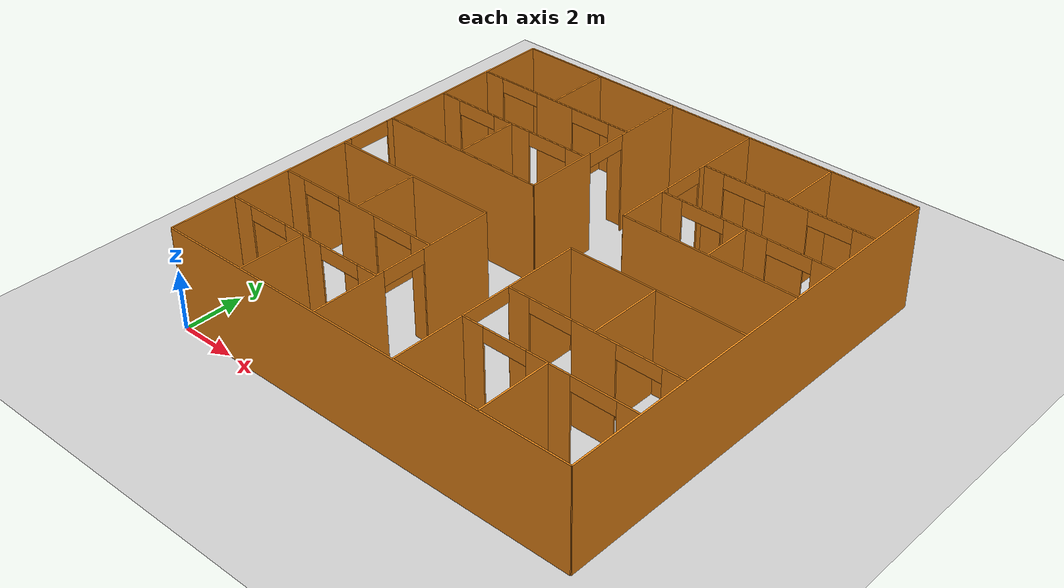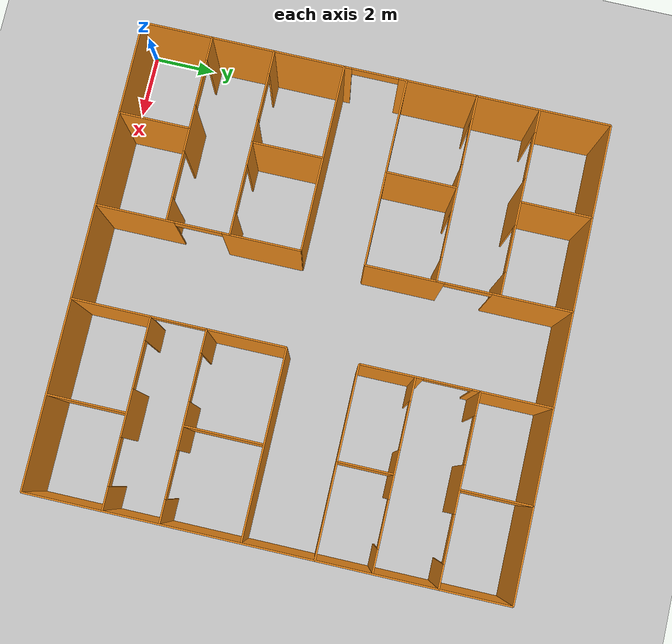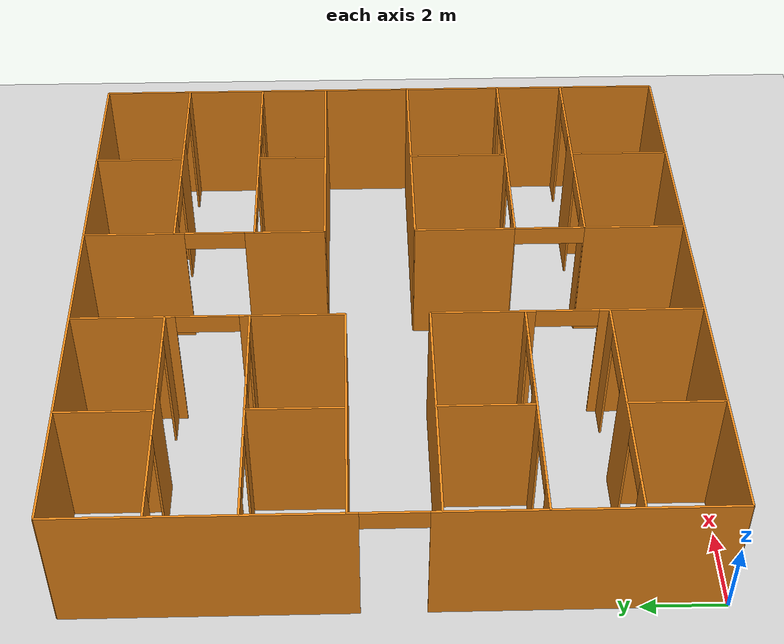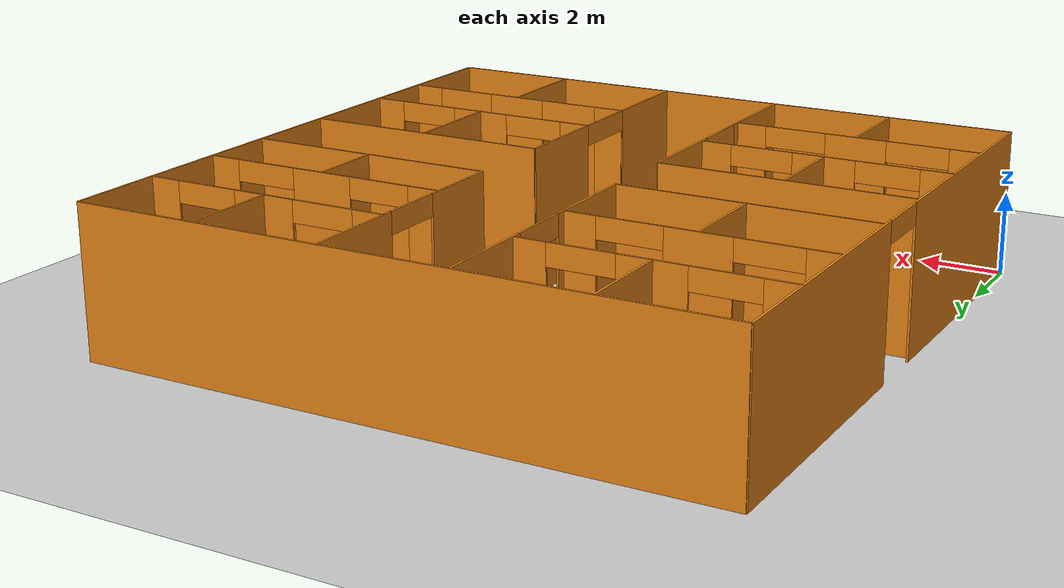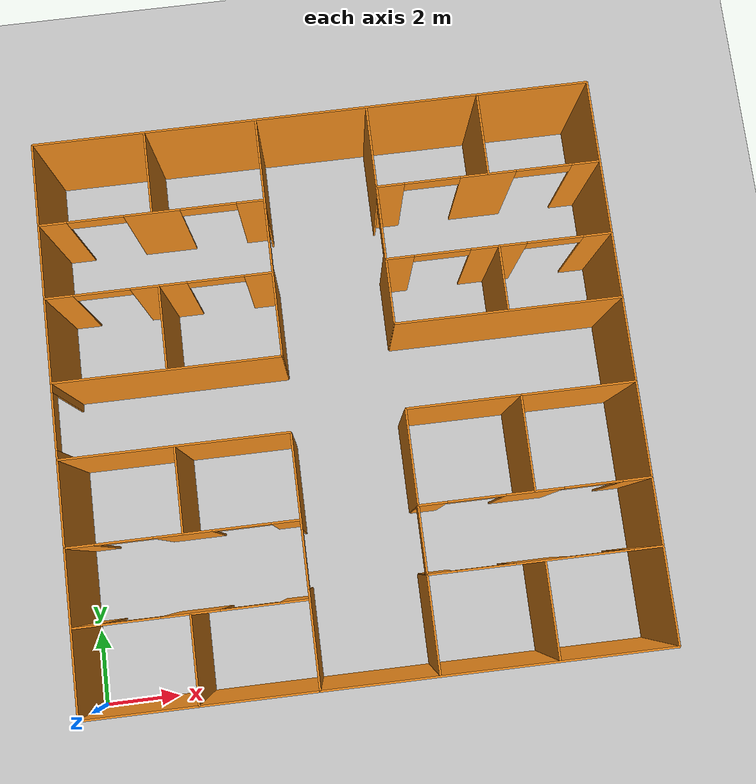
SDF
<sdf version="1.6">
  <world name="default">
    <model name="box_70">
  <pose frame="">1.5 10.75 3.25 0 0 -0.0</pose>
  <link name="link">
    <inertial>
      <mass>1</mass>
      <inertia>
        <ixx>0</ixx>
        <ixy>0</ixy>
        <ixz>0</ixz>
        <iyy>0</iyy>
        <iyz>0</iyz>
        <izz>0</izz>
      </inertia>
    </inertial>
    <collision name="collision">
      <geometry>
        <box>
          <size>1.5 0.05 0.5</size>
        </box>
      </geometry>
      <max_contacts>10</max_contacts>
      <surface>
        <contact>
          <ode/>
        </contact>
        <bounce/>
        <friction>
          <torsional>
            <ode/>
          </torsional>
          <ode/>
        </friction>
      </surface>
    </collision>
    <visual name="visual">
      <geometry>
        <box>
          <size>1.5 0.05 0.5</size>
        </box>
      </geometry>
      <material>
        <script>
          <name>Gazebo/Orange</name>
          <uri>file://media/materials/scripts/gazebo.material</uri>
        </script>
      </material>
    </visual>
    <self_collide>0</self_collide>
    <enable_wind>0</enable_wind>
    <kinematic>0</kinematic>
  </link>
	<static>1</static>
</model><model name="box_69">
  <pose frame="">4.5 10.75 3.25 0 0 -0.0</pose>
  <link name="link">
    <inertial>
      <mass>1</mass>
      <inertia>
        <ixx>0</ixx>
        <ixy>0</ixy>
        <ixz>0</ixz>
        <iyy>0</iyy>
        <iyz>0</iyz>
        <izz>0</izz>
      </inertia>
    </inertial>
    <collision name="collision">
      <geometry>
        <box>
          <size>1.5 0.05 0.5</size>
        </box>
      </geometry>
      <max_contacts>10</max_contacts>
      <surface>
        <contact>
          <ode/>
        </contact>
        <bounce/>
        <friction>
          <torsional>
            <ode/>
          </torsional>
          <ode/>
        </friction>
      </surface>
    </collision>
    <visual name="visual">
      <geometry>
        <box>
          <size>1.5 0.05 0.5</size>
        </box>
      </geometry>
      <material>
        <script>
          <name>Gazebo/Orange</name>
          <uri>file://media/materials/scripts/gazebo.material</uri>
        </script>
      </material>
    </visual>
    <self_collide>0</self_collide>
    <enable_wind>0</enable_wind>
    <kinematic>0</kinematic>
  </link>
	<static>1</static>
</model><model name="box_68">
  <pose frame="">10.5 10.75 3.25 0 0 -3.141592653589793</pose>
  <link name="link">
    <inertial>
      <mass>1</mass>
      <inertia>
        <ixx>0</ixx>
        <ixy>0</ixy>
        <ixz>0</ixz>
        <iyy>0</iyy>
        <iyz>0</iyz>
        <izz>0</izz>
      </inertia>
    </inertial>
    <collision name="collision">
      <geometry>
        <box>
          <size>1.5 0.05 0.5</size>
        </box>
      </geometry>
      <max_contacts>10</max_contacts>
      <surface>
        <contact>
          <ode/>
        </contact>
        <bounce/>
        <friction>
          <torsional>
            <ode/>
          </torsional>
          <ode/>
        </friction>
      </surface>
    </collision>
    <visual name="visual">
      <geometry>
        <box>
          <size>1.5 0.05 0.5</size>
        </box>
      </geometry>
      <material>
        <script>
          <name>Gazebo/Orange</name>
          <uri>file://media/materials/scripts/gazebo.material</uri>
        </script>
      </material>
    </visual>
    <self_collide>0</self_collide>
    <enable_wind>0</enable_wind>
    <kinematic>0</kinematic>
  </link>
	<static>1</static>
</model><model name="box_67">
  <pose frame="">13.5 10.75 3.25 0 0 -3.141592653589793</pose>
  <link name="link">
    <inertial>
      <mass>1</mass>
      <inertia>
        <ixx>0</ixx>
        <ixy>0</ixy>
        <ixz>0</ixz>
        <iyy>0</iyy>
        <iyz>0</iyz>
        <izz>0</izz>
      </inertia>
    </inertial>
    <collision name="collision">
      <geometry>
        <box>
          <size>1.5 0.05 0.5</size>
        </box>
      </geometry>
      <max_contacts>10</max_contacts>
      <surface>
        <contact>
          <ode/>
        </contact>
        <bounce/>
        <friction>
          <torsional>
            <ode/>
          </torsional>
          <ode/>
        </friction>
      </surface>
    </collision>
    <visual name="visual">
      <geometry>
        <box>
          <size>1.5 0.05 0.5</size>
        </box>
      </geometry>
      <material>
        <script>
          <name>Gazebo/Orange</name>
          <uri>file://media/materials/scripts/gazebo.material</uri>
        </script>
      </material>
    </visual>
    <self_collide>0</self_collide>
    <enable_wind>0</enable_wind>
    <kinematic>0</kinematic>
  </link>
	<static>1</static>
</model><model name="box_66">
  <pose frame="">13.5 12.75 3.25 0 0 -3.141592653589793</pose>
  <link name="link">
    <inertial>
      <mass>1</mass>
      <inertia>
        <ixx>0</ixx>
        <ixy>0</ixy>
        <ixz>0</ixz>
        <iyy>0</iyy>
        <iyz>0</iyz>
        <izz>0</izz>
      </inertia>
    </inertial>
    <collision name="collision">
      <geometry>
        <box>
          <size>1.5 0.05 0.5</size>
        </box>
      </geometry>
      <max_contacts>10</max_contacts>
      <surface>
        <contact>
          <ode/>
        </contact>
        <bounce/>
        <friction>
          <torsional>
            <ode/>
          </torsional>
          <ode/>
        </friction>
      </surface>
    </collision>
    <visual name="visual">
      <geometry>
        <box>
          <size>1.5 0.05 0.5</size>
        </box>
      </geometry>
      <material>
        <script>
          <name>Gazebo/Orange</name>
          <uri>file://media/materials/scripts/gazebo.material</uri>
        </script>
      </material>
    </visual>
    <self_collide>0</self_collide>
    <enable_wind>0</enable_wind>
    <kinematic>0</kinematic>
  </link>
	<static>1</static>
</model><model name="box_65">
  <pose frame="">10.5 12.75 3.25 0 0 -3.141592653589793</pose>
  <link name="link">
    <inertial>
      <mass>1</mass>
      <inertia>
        <ixx>0</ixx>
        <ixy>0</ixy>
        <ixz>0</ixz>
        <iyy>0</iyy>
        <iyz>0</iyz>
        <izz>0</izz>
      </inertia>
    </inertial>
    <collision name="collision">
      <geometry>
        <box>
          <size>1.5 0.05 0.5</size>
        </box>
      </geometry>
      <max_contacts>10</max_contacts>
      <surface>
        <contact>
          <ode/>
        </contact>
        <bounce/>
        <friction>
          <torsional>
            <ode/>
          </torsional>
          <ode/>
        </friction>
      </surface>
    </collision>
    <visual name="visual">
      <geometry>
        <box>
          <size>1.5 0.05 0.5</size>
        </box>
      </geometry>
      <material>
        <script>
          <name>Gazebo/Orange</name>
          <uri>file://media/materials/scripts/gazebo.material</uri>
        </script>
      </material>
    </visual>
    <self_collide>0</self_collide>
    <enable_wind>0</enable_wind>
    <kinematic>0</kinematic>
  </link>
	<static>1</static>
</model><model name="box_64">
  <pose frame="">9.0 11.75 3.25 0 0 1.5707963267948966</pose>
  <link name="link">
    <inertial>
      <mass>1</mass>
      <inertia>
        <ixx>0</ixx>
        <ixy>0</ixy>
        <ixz>0</ixz>
        <iyy>0</iyy>
        <iyz>0</iyz>
        <izz>0</izz>
      </inertia>
    </inertial>
    <collision name="collision">
      <geometry>
        <box>
          <size>1.5 0.05 0.5</size>
        </box>
      </geometry>
      <max_contacts>10</max_contacts>
      <surface>
        <contact>
          <ode/>
        </contact>
        <bounce/>
        <friction>
          <torsional>
            <ode/>
          </torsional>
          <ode/>
        </friction>
      </surface>
    </collision>
    <visual name="visual">
      <geometry>
        <box>
          <size>1.5 0.05 0.5</size>
        </box>
      </geometry>
      <material>
        <script>
          <name>Gazebo/Orange</name>
          <uri>file://media/materials/scripts/gazebo.material</uri>
        </script>
      </material>
    </visual>
    <self_collide>0</self_collide>
    <enable_wind>0</enable_wind>
    <kinematic>0</kinematic>
  </link>
	<static>1</static>
</model><model name="box_63">
  <pose frame="">6.0 11.75 3.25 0 0 -1.5707963267948966</pose>
  <link name="link">
    <inertial>
      <mass>1</mass>
      <inertia>
        <ixx>0</ixx>
        <ixy>0</ixy>
        <ixz>0</ixz>
        <iyy>0</iyy>
        <iyz>0</iyz>
        <izz>0</izz>
      </inertia>
    </inertial>
    <collision name="collision">
      <geometry>
        <box>
          <size>1.5 0.05 0.5</size>
        </box>
      </geometry>
      <max_contacts>10</max_contacts>
      <surface>
        <contact>
          <ode/>
        </contact>
        <bounce/>
        <friction>
          <torsional>
            <ode/>
          </torsional>
          <ode/>
        </friction>
      </surface>
    </collision>
    <visual name="visual">
      <geometry>
        <box>
          <size>1.5 0.05 0.5</size>
        </box>
      </geometry>
      <material>
        <script>
          <name>Gazebo/Orange</name>
          <uri>file://media/materials/scripts/gazebo.material</uri>
        </script>
      </material>
    </visual>
    <self_collide>0</self_collide>
    <enable_wind>0</enable_wind>
    <kinematic>0</kinematic>
  </link>
	<static>1</static>
</model><model name="box_62">
  <pose frame="">4.5 12.75 3.25 0 0 -3.141592653589793</pose>
  <link name="link">
    <inertial>
      <mass>1</mass>
      <inertia>
        <ixx>0</ixx>
        <ixy>0</ixy>
        <ixz>0</ixz>
        <iyy>0</iyy>
        <iyz>0</iyz>
        <izz>0</izz>
      </inertia>
    </inertial>
    <collision name="collision">
      <geometry>
        <box>
          <size>1.5 0.05 0.5</size>
        </box>
      </geometry>
      <max_contacts>10</max_contacts>
      <surface>
        <contact>
          <ode/>
        </contact>
        <bounce/>
        <friction>
          <torsional>
            <ode/>
          </torsional>
          <ode/>
        </friction>
      </surface>
    </collision>
    <visual name="visual">
      <geometry>
        <box>
          <size>1.5 0.05 0.5</size>
        </box>
      </geometry>
      <material>
        <script>
          <name>Gazebo/Orange</name>
          <uri>file://media/materials/scripts/gazebo.material</uri>
        </script>
      </material>
    </visual>
    <self_collide>0</self_collide>
    <enable_wind>0</enable_wind>
    <kinematic>0</kinematic>
  </link>
	<static>1</static>
</model><model name="box_61">
  <pose frame="">1.5 12.75 3.25 0 0 -3.141592653589793</pose>
  <link name="link">
    <inertial>
      <mass>1</mass>
      <inertia>
        <ixx>0</ixx>
        <ixy>0</ixy>
        <ixz>0</ixz>
        <iyy>0</iyy>
        <iyz>0</iyz>
        <izz>0</izz>
      </inertia>
    </inertial>
    <collision name="collision">
      <geometry>
        <box>
          <size>1.5 0.05 0.5</size>
        </box>
      </geometry>
      <max_contacts>10</max_contacts>
      <surface>
        <contact>
          <ode/>
        </contact>
        <bounce/>
        <friction>
          <torsional>
            <ode/>
          </torsional>
          <ode/>
        </friction>
      </surface>
    </collision>
    <visual name="visual">
      <geometry>
        <box>
          <size>1.5 0.05 0.5</size>
        </box>
      </geometry>
      <material>
        <script>
          <name>Gazebo/Orange</name>
          <uri>file://media/materials/scripts/gazebo.material</uri>
        </script>
      </material>
    </visual>
    <self_collide>0</self_collide>
    <enable_wind>0</enable_wind>
    <kinematic>0</kinematic>
  </link>
	<static>1</static>
</model><model name="box_60">
  <pose frame="">4.5 2.25 3.25 0 0 -3.141592653589793</pose>
  <link name="link">
    <inertial>
      <mass>1</mass>
      <inertia>
        <ixx>0</ixx>
        <ixy>0</ixy>
        <ixz>0</ixz>
        <iyy>0</iyy>
        <iyz>0</iyz>
        <izz>0</izz>
      </inertia>
    </inertial>
    <collision name="collision">
      <geometry>
        <box>
          <size>1.5 0.05 0.5</size>
        </box>
      </geometry>
      <max_contacts>10</max_contacts>
      <surface>
        <contact>
          <ode/>
        </contact>
        <bounce/>
        <friction>
          <torsional>
            <ode/>
          </torsional>
          <ode/>
        </friction>
      </surface>
    </collision>
    <visual name="visual">
      <geometry>
        <box>
          <size>1.5 0.05 0.5</size>
        </box>
      </geometry>
      <material>
        <script>
          <name>Gazebo/Orange</name>
          <uri>file://media/materials/scripts/gazebo.material</uri>
        </script>
      </material>
    </visual>
    <self_collide>0</self_collide>
    <enable_wind>0</enable_wind>
    <kinematic>0</kinematic>
  </link>
	<static>1</static>
</model><model name="box_59">
  <pose frame="">1.5 2.25 3.25 0 0 -3.141592653589793</pose>
  <link name="link">
    <inertial>
      <mass>1</mass>
      <inertia>
        <ixx>0</ixx>
        <ixy>0</ixy>
        <ixz>0</ixz>
        <iyy>0</iyy>
        <iyz>0</iyz>
        <izz>0</izz>
      </inertia>
    </inertial>
    <collision name="collision">
      <geometry>
        <box>
          <size>1.5 0.05 0.5</size>
        </box>
      </geometry>
      <max_contacts>10</max_contacts>
      <surface>
        <contact>
          <ode/>
        </contact>
        <bounce/>
        <friction>
          <torsional>
            <ode/>
          </torsional>
          <ode/>
        </friction>
      </surface>
    </collision>
    <visual name="visual">
      <geometry>
        <box>
          <size>1.5 0.05 0.5</size>
        </box>
      </geometry>
      <material>
        <script>
          <name>Gazebo/Orange</name>
          <uri>file://media/materials/scripts/gazebo.material</uri>
        </script>
      </material>
    </visual>
    <self_collide>0</self_collide>
    <enable_wind>0</enable_wind>
    <kinematic>0</kinematic>
  </link>
	<static>1</static>
</model><model name="box_58">
  <pose frame="">0.0 7.5 3.25 0 0 -1.5707963267948966</pose>
  <link name="link">
    <inertial>
      <mass>1</mass>
      <inertia>
        <ixx>0</ixx>
        <ixy>0</ixy>
        <ixz>0</ixz>
        <iyy>0</iyy>
        <iyz>0</iyz>
        <izz>0</izz>
      </inertia>
    </inertial>
    <collision name="collision">
      <geometry>
        <box>
          <size>1.5 0.05 0.5</size>
        </box>
      </geometry>
      <max_contacts>10</max_contacts>
      <surface>
        <contact>
          <ode/>
        </contact>
        <bounce/>
        <friction>
          <torsional>
            <ode/>
          </torsional>
          <ode/>
        </friction>
      </surface>
    </collision>
    <visual name="visual">
      <geometry>
        <box>
          <size>1.5 0.05 0.5</size>
        </box>
      </geometry>
      <material>
        <script>
          <name>Gazebo/Orange</name>
          <uri>file://media/materials/scripts/gazebo.material</uri>
        </script>
      </material>
    </visual>
    <self_collide>0</self_collide>
    <enable_wind>0</enable_wind>
    <kinematic>0</kinematic>
  </link>
	<static>1</static>
</model><model name="box_57">
  <pose frame="">6.0 3.25 3.25 0 0 -1.5707963267948966</pose>
  <link name="link">
    <inertial>
      <mass>1</mass>
      <inertia>
        <ixx>0</ixx>
        <ixy>0</ixy>
        <ixz>0</ixz>
        <iyy>0</iyy>
        <iyz>0</iyz>
        <izz>0</izz>
      </inertia>
    </inertial>
    <collision name="collision">
      <geometry>
        <box>
          <size>1.5 0.05 0.5</size>
        </box>
      </geometry>
      <max_contacts>10</max_contacts>
      <surface>
        <contact>
          <ode/>
        </contact>
        <bounce/>
        <friction>
          <torsional>
            <ode/>
          </torsional>
          <ode/>
        </friction>
      </surface>
    </collision>
    <visual name="visual">
      <geometry>
        <box>
          <size>1.5 0.05 0.5</size>
        </box>
      </geometry>
      <material>
        <script>
          <name>Gazebo/Orange</name>
          <uri>file://media/materials/scripts/gazebo.material</uri>
        </script>
      </material>
    </visual>
    <self_collide>0</self_collide>
    <enable_wind>0</enable_wind>
    <kinematic>0</kinematic>
  </link>
	<static>1</static>
</model><model name="box_56">
  <pose frame="">10.5 4.25 3.25 0 0 -3.141592653589793</pose>
  <link name="link">
    <inertial>
      <mass>1</mass>
      <inertia>
        <ixx>0</ixx>
        <ixy>0</ixy>
        <ixz>0</ixz>
        <iyy>0</iyy>
        <iyz>0</iyz>
        <izz>0</izz>
      </inertia>
    </inertial>
    <collision name="collision">
      <geometry>
        <box>
          <size>1.5 0.05 0.5</size>
        </box>
      </geometry>
      <max_contacts>10</max_contacts>
      <surface>
        <contact>
          <ode/>
        </contact>
        <bounce/>
        <friction>
          <torsional>
            <ode/>
          </torsional>
          <ode/>
        </friction>
      </surface>
    </collision>
    <visual name="visual">
      <geometry>
        <box>
          <size>1.5 0.05 0.5</size>
        </box>
      </geometry>
      <material>
        <script>
          <name>Gazebo/Orange</name>
          <uri>file://media/materials/scripts/gazebo.material</uri>
        </script>
      </material>
    </visual>
    <self_collide>0</self_collide>
    <enable_wind>0</enable_wind>
    <kinematic>0</kinematic>
  </link>
	<static>1</static>
</model><model name="box_55">
  <pose frame="">10.5 2.5 3.25 0 0 -3.141592653589793</pose>
  <link name="link">
    <inertial>
      <mass>1</mass>
      <inertia>
        <ixx>0</ixx>
        <ixy>0</ixy>
        <ixz>0</ixz>
        <iyy>0</iyy>
        <iyz>0</iyz>
        <izz>0</izz>
      </inertia>
    </inertial>
    <collision name="collision">
      <geometry>
        <box>
          <size>1.5 0.05 0.5</size>
        </box>
      </geometry>
      <max_contacts>10</max_contacts>
      <surface>
        <contact>
          <ode/>
        </contact>
        <bounce/>
        <friction>
          <torsional>
            <ode/>
          </torsional>
          <ode/>
        </friction>
      </surface>
    </collision>
    <visual name="visual">
      <geometry>
        <box>
          <size>1.5 0.05 0.5</size>
        </box>
      </geometry>
      <material>
        <script>
          <name>Gazebo/Orange</name>
          <uri>file://media/materials/scripts/gazebo.material</uri>
        </script>
      </material>
    </visual>
    <self_collide>0</self_collide>
    <enable_wind>0</enable_wind>
    <kinematic>0</kinematic>
  </link>
	<static>1</static>
</model><model name="box_54">
  <pose frame="">1.5 4.25 3.25 0 0 -0.0</pose>
  <link name="link">
    <inertial>
      <mass>1</mass>
      <inertia>
        <ixx>0</ixx>
        <ixy>0</ixy>
        <ixz>0</ixz>
        <iyy>0</iyy>
        <iyz>0</iyz>
        <izz>0</izz>
      </inertia>
    </inertial>
    <collision name="collision">
      <geometry>
        <box>
          <size>1.5 0.05 0.5</size>
        </box>
      </geometry>
      <max_contacts>10</max_contacts>
      <surface>
        <contact>
          <ode/>
        </contact>
        <bounce/>
        <friction>
          <torsional>
            <ode/>
          </torsional>
          <ode/>
        </friction>
      </surface>
    </collision>
    <visual name="visual">
      <geometry>
        <box>
          <size>1.5 0.05 0.5</size>
        </box>
      </geometry>
      <material>
        <script>
          <name>Gazebo/Orange</name>
          <uri>file://media/materials/scripts/gazebo.material</uri>
        </script>
      </material>
    </visual>
    <self_collide>0</self_collide>
    <enable_wind>0</enable_wind>
    <kinematic>0</kinematic>
  </link>
	<static>1</static>
</model><model name="box_53">
  <pose frame="">4.5 4.25 3.25 0 0 -0.0</pose>
  <link name="link">
    <inertial>
      <mass>1</mass>
      <inertia>
        <ixx>0</ixx>
        <ixy>0</ixy>
        <ixz>0</ixz>
        <iyy>0</iyy>
        <iyz>0</iyz>
        <izz>0</izz>
      </inertia>
    </inertial>
    <collision name="collision">
      <geometry>
        <box>
          <size>1.5 0.05 0.5</size>
        </box>
      </geometry>
      <max_contacts>10</max_contacts>
      <surface>
        <contact>
          <ode/>
        </contact>
        <bounce/>
        <friction>
          <torsional>
            <ode/>
          </torsional>
          <ode/>
        </friction>
      </surface>
    </collision>
    <visual name="visual">
      <geometry>
        <box>
          <size>1.5 0.05 0.5</size>
        </box>
      </geometry>
      <material>
        <script>
          <name>Gazebo/Orange</name>
          <uri>file://media/materials/scripts/gazebo.material</uri>
        </script>
      </material>
    </visual>
    <self_collide>0</self_collide>
    <enable_wind>0</enable_wind>
    <kinematic>0</kinematic>
  </link>
	<static>1</static>
</model><model name="box_52">
  <pose frame="">9.0 3.375 3.25 0 0 1.5707963267948966</pose>
  <link name="link">
    <inertial>
      <mass>1</mass>
      <inertia>
        <ixx>0</ixx>
        <ixy>0</ixy>
        <ixz>0</ixz>
        <iyy>0</iyy>
        <iyz>0</iyz>
        <izz>0</izz>
      </inertia>
    </inertial>
    <collision name="collision">
      <geometry>
        <box>
          <size>1.75 0.05 0.5</size>
        </box>
      </geometry>
      <max_contacts>10</max_contacts>
      <surface>
        <contact>
          <ode/>
        </contact>
        <bounce/>
        <friction>
          <torsional>
            <ode/>
          </torsional>
          <ode/>
        </friction>
      </surface>
    </collision>
    <visual name="visual">
      <geometry>
        <box>
          <size>1.75 0.05 0.5</size>
        </box>
      </geometry>
      <material>
        <script>
          <name>Gazebo/Orange</name>
          <uri>file://media/materials/scripts/gazebo.material</uri>
        </script>
      </material>
    </visual>
    <self_collide>0</self_collide>
    <enable_wind>0</enable_wind>
    <kinematic>0</kinematic>
  </link>
	<static>1</static>
</model><model name="box_51">
  <pose frame="">13.5 2.5 3.25 0 0 -3.141592653589793</pose>
  <link name="link">
    <inertial>
      <mass>1</mass>
      <inertia>
        <ixx>0</ixx>
        <ixy>0</ixy>
        <ixz>0</ixz>
        <iyy>0</iyy>
        <iyz>0</iyz>
        <izz>0</izz>
      </inertia>
    </inertial>
    <collision name="collision">
      <geometry>
        <box>
          <size>1.5 0.05 0.5</size>
        </box>
      </geometry>
      <max_contacts>10</max_contacts>
      <surface>
        <contact>
          <ode/>
        </contact>
        <bounce/>
        <friction>
          <torsional>
            <ode/>
          </torsional>
          <ode/>
        </friction>
      </surface>
    </collision>
    <visual name="visual">
      <geometry>
        <box>
          <size>1.5 0.05 0.5</size>
        </box>
      </geometry>
      <material>
        <script>
          <name>Gazebo/Orange</name>
          <uri>file://media/materials/scripts/gazebo.material</uri>
        </script>
      </material>
    </visual>
    <self_collide>0</self_collide>
    <enable_wind>0</enable_wind>
    <kinematic>0</kinematic>
  </link>
	<static>1</static>
</model><model name="box_50">
  <pose frame="">13.5 4.25 3.25 0 0 -3.141592653589793</pose>
  <link name="link">
    <inertial>
      <mass>1</mass>
      <inertia>
        <ixx>0</ixx>
        <ixy>0</ixy>
        <ixz>0</ixz>
        <iyy>0</iyy>
        <iyz>0</iyz>
        <izz>0</izz>
      </inertia>
    </inertial>
    <collision name="collision">
      <geometry>
        <box>
          <size>1.5 0.05 0.5</size>
        </box>
      </geometry>
      <max_contacts>10</max_contacts>
      <surface>
        <contact>
          <ode/>
        </contact>
        <bounce/>
        <friction>
          <torsional>
            <ode/>
          </torsional>
          <ode/>
        </friction>
      </surface>
    </collision>
    <visual name="visual">
      <geometry>
        <box>
          <size>1.5 0.05 0.5</size>
        </box>
      </geometry>
      <material>
        <script>
          <name>Gazebo/Orange</name>
          <uri>file://media/materials/scripts/gazebo.material</uri>
        </script>
      </material>
    </visual>
    <self_collide>0</self_collide>
    <enable_wind>0</enable_wind>
    <kinematic>0</kinematic>
  </link>
	<static>1</static>
</model><model name="box_49">
  <pose frame="">9.0 13.75 1.75 0 0 -1.5707963267948966</pose>
  <link name="link">
    <inertial>
      <mass>1</mass>
      <inertia>
        <ixx>0</ixx>
        <ixy>0</ixy>
        <ixz>0</ixz>
        <iyy>0</iyy>
        <iyz>0</iyz>
        <izz>0</izz>
      </inertia>
    </inertial>
    <collision name="collision">
      <geometry>
        <box>
          <size>2.5 0.05 3.5</size>
        </box>
      </geometry>
      <max_contacts>10</max_contacts>
      <surface>
        <contact>
          <ode/>
        </contact>
        <bounce/>
        <friction>
          <torsional>
            <ode/>
          </torsional>
          <ode/>
        </friction>
      </surface>
    </collision>
    <visual name="visual">
      <geometry>
        <box>
          <size>2.5 0.05 3.5</size>
        </box>
      </geometry>
      <material>
        <script>
          <name>Gazebo/Orange</name>
          <uri>file://media/materials/scripts/gazebo.material</uri>
        </script>
      </material>
    </visual>
    <self_collide>0</self_collide>
    <enable_wind>0</enable_wind>
    <kinematic>0</kinematic>
  </link>
	<static>1</static>
</model><model name="box_48">
  <pose frame="">9.0 10.0 1.75 0 0 -1.5707963267948966</pose>
  <link name="link">
    <inertial>
      <mass>1</mass>
      <inertia>
        <ixx>0</ixx>
        <ixy>0</ixy>
        <ixz>0</ixz>
        <iyy>0</iyy>
        <iyz>0</iyz>
        <izz>0</izz>
      </inertia>
    </inertial>
    <collision name="collision">
      <geometry>
        <box>
          <size>2.0 0.05 3.5</size>
        </box>
      </geometry>
      <max_contacts>10</max_contacts>
      <surface>
        <contact>
          <ode/>
        </contact>
        <bounce/>
        <friction>
          <torsional>
            <ode/>
          </torsional>
          <ode/>
        </friction>
      </surface>
    </collision>
    <visual name="visual">
      <geometry>
        <box>
          <size>2.0 0.05 3.5</size>
        </box>
      </geometry>
      <material>
        <script>
          <name>Gazebo/Orange</name>
          <uri>file://media/materials/scripts/gazebo.material</uri>
        </script>
      </material>
    </visual>
    <self_collide>0</self_collide>
    <enable_wind>0</enable_wind>
    <kinematic>0</kinematic>
  </link>
	<static>1</static>
</model><model name="box_47">
  <pose frame="">12.0 4.25 1.75 0 0 -3.141592653589793</pose>
  <link name="link">
    <inertial>
      <mass>1</mass>
      <inertia>
        <ixx>0</ixx>
        <ixy>0</ixy>
        <ixz>0</ixz>
        <iyy>0</iyy>
        <iyz>0</iyz>
        <izz>0</izz>
      </inertia>
    </inertial>
    <collision name="collision">
      <geometry>
        <box>
          <size>1.5 0.05 3.5</size>
        </box>
      </geometry>
      <max_contacts>10</max_contacts>
      <surface>
        <contact>
          <ode/>
        </contact>
        <bounce/>
        <friction>
          <torsional>
            <ode/>
          </torsional>
          <ode/>
        </friction>
      </surface>
    </collision>
    <visual name="visual">
      <geometry>
        <box>
          <size>1.5 0.05 3.5</size>
        </box>
      </geometry>
      <material>
        <script>
          <name>Gazebo/Orange</name>
          <uri>file://media/materials/scripts/gazebo.material</uri>
        </script>
      </material>
    </visual>
    <self_collide>0</self_collide>
    <enable_wind>0</enable_wind>
    <kinematic>0</kinematic>
  </link>
	<static>1</static>
</model><model name="box_46">
  <pose frame="">12.0 10.75 1.75 0 0 -3.141592653589793</pose>
  <link name="link">
    <inertial>
      <mass>1</mass>
      <inertia>
        <ixx>0</ixx>
        <ixy>0</ixy>
        <ixz>0</ixz>
        <iyy>0</iyy>
        <iyz>0</iyz>
        <izz>0</izz>
      </inertia>
    </inertial>
    <collision name="collision">
      <geometry>
        <box>
          <size>1.5 0.05 3.5</size>
        </box>
      </geometry>
      <max_contacts>10</max_contacts>
      <surface>
        <contact>
          <ode/>
        </contact>
        <bounce/>
        <friction>
          <torsional>
            <ode/>
          </torsional>
          <ode/>
        </friction>
      </surface>
    </collision>
    <visual name="visual">
      <geometry>
        <box>
          <size>1.5 0.05 3.5</size>
        </box>
      </geometry>
      <material>
        <script>
          <name>Gazebo/Orange</name>
          <uri>file://media/materials/scripts/gazebo.material</uri>
        </script>
      </material>
    </visual>
    <self_collide>0</self_collide>
    <enable_wind>0</enable_wind>
    <kinematic>0</kinematic>
  </link>
	<static>1</static>
</model><model name="box_45">
  <pose frame="">5.625 10.75 1.75 0 0 -3.141592653589793</pose>
  <link name="link">
    <inertial>
      <mass>1</mass>
      <inertia>
        <ixx>0</ixx>
        <ixy>0</ixy>
        <ixz>0</ixz>
        <iyy>0</iyy>
        <iyz>0</iyz>
        <izz>0</izz>
      </inertia>
    </inertial>
    <collision name="collision">
      <geometry>
        <box>
          <size>0.75 0.05 3.5</size>
        </box>
      </geometry>
      <max_contacts>10</max_contacts>
      <surface>
        <contact>
          <ode/>
        </contact>
        <bounce/>
        <friction>
          <torsional>
            <ode/>
          </torsional>
          <ode/>
        </friction>
      </surface>
    </collision>
    <visual name="visual">
      <geometry>
        <box>
          <size>0.75 0.05 3.5</size>
        </box>
      </geometry>
      <material>
        <script>
          <name>Gazebo/Orange</name>
          <uri>file://media/materials/scripts/gazebo.material</uri>
        </script>
      </material>
    </visual>
    <self_collide>0</self_collide>
    <enable_wind>0</enable_wind>
    <kinematic>0</kinematic>
  </link>
	<static>1</static>
</model><model name="box_44">
  <pose frame="">3.0 10.75 1.75 0 0 -3.141592653589793</pose>
  <link name="link">
    <inertial>
      <mass>1</mass>
      <inertia>
        <ixx>0</ixx>
        <ixy>0</ixy>
        <ixz>0</ixz>
        <iyy>0</iyy>
        <iyz>0</iyz>
        <izz>0</izz>
      </inertia>
    </inertial>
    <collision name="collision">
      <geometry>
        <box>
          <size>1.5 0.05 3.5</size>
        </box>
      </geometry>
      <max_contacts>10</max_contacts>
      <surface>
        <contact>
          <ode/>
        </contact>
        <bounce/>
        <friction>
          <torsional>
            <ode/>
          </torsional>
          <ode/>
        </friction>
      </surface>
    </collision>
    <visual name="visual">
      <geometry>
        <box>
          <size>1.5 0.05 3.5</size>
        </box>
      </geometry>
      <material>
        <script>
          <name>Gazebo/Orange</name>
          <uri>file://media/materials/scripts/gazebo.material</uri>
        </script>
      </material>
    </visual>
    <self_collide>0</self_collide>
    <enable_wind>0</enable_wind>
    <kinematic>0</kinematic>
  </link>
	<static>1</static>
</model><model name="box_43">
  <pose frame="">0.375 10.75 1.75 0 0 -3.141592653589793</pose>
  <link name="link">
    <inertial>
      <mass>1</mass>
      <inertia>
        <ixx>0</ixx>
        <ixy>0</ixy>
        <ixz>0</ixz>
        <iyy>0</iyy>
        <iyz>0</iyz>
        <izz>0</izz>
      </inertia>
    </inertial>
    <collision name="collision">
      <geometry>
        <box>
          <size>0.75 0.05 3.5</size>
        </box>
      </geometry>
      <max_contacts>10</max_contacts>
      <surface>
        <contact>
          <ode/>
        </contact>
        <bounce/>
        <friction>
          <torsional>
            <ode/>
          </torsional>
          <ode/>
        </friction>
      </surface>
    </collision>
    <visual name="visual">
      <geometry>
        <box>
          <size>0.75 0.05 3.5</size>
        </box>
      </geometry>
      <material>
        <script>
          <name>Gazebo/Orange</name>
          <uri>file://media/materials/scripts/gazebo.material</uri>
        </script>
      </material>
    </visual>
    <self_collide>0</self_collide>
    <enable_wind>0</enable_wind>
    <kinematic>0</kinematic>
  </link>
	<static>1</static>
</model><model name="box_42">
  <pose frame="">12.0 9.875 1.75 0 0 1.5707963267948966</pose>
  <link name="link">
    <inertial>
      <mass>1</mass>
      <inertia>
        <ixx>0</ixx>
        <ixy>0</ixy>
        <ixz>0</ixz>
        <iyy>0</iyy>
        <iyz>0</iyz>
        <izz>0</izz>
      </inertia>
    </inertial>
    <collision name="collision">
      <geometry>
        <box>
          <size>1.75 0.05 3.5</size>
        </box>
      </geometry>
      <max_contacts>10</max_contacts>
      <surface>
        <contact>
          <ode/>
        </contact>
        <bounce/>
        <friction>
          <torsional>
            <ode/>
          </torsional>
          <ode/>
        </friction>
      </surface>
    </collision>
    <visual name="visual">
      <geometry>
        <box>
          <size>1.75 0.05 3.5</size>
        </box>
      </geometry>
      <material>
        <script>
          <name>Gazebo/Orange</name>
          <uri>file://media/materials/scripts/gazebo.material</uri>
        </script>
      </material>
    </visual>
    <self_collide>0</self_collide>
    <enable_wind>0</enable_wind>
    <kinematic>0</kinematic>
  </link>
	<static>1</static>
</model><model name="box_41">
  <pose frame="">12.0 13.875 1.75 0 0 -1.5707963267948966</pose>
  <link name="link">
    <inertial>
      <mass>1</mass>
      <inertia>
        <ixx>0</ixx>
        <ixy>0</ixy>
        <ixz>0</ixz>
        <iyy>0</iyy>
        <iyz>0</iyz>
        <izz>0</izz>
      </inertia>
    </inertial>
    <collision name="collision">
      <geometry>
        <box>
          <size>2.25 0.05 3.5</size>
        </box>
      </geometry>
      <max_contacts>10</max_contacts>
      <surface>
        <contact>
          <ode/>
        </contact>
        <bounce/>
        <friction>
          <torsional>
            <ode/>
          </torsional>
          <ode/>
        </friction>
      </surface>
    </collision>
    <visual name="visual">
      <geometry>
        <box>
          <size>2.25 0.05 3.5</size>
        </box>
      </geometry>
      <material>
        <script>
          <name>Gazebo/Orange</name>
          <uri>file://media/materials/scripts/gazebo.material</uri>
        </script>
      </material>
    </visual>
    <self_collide>0</self_collide>
    <enable_wind>0</enable_wind>
    <kinematic>0</kinematic>
  </link>
	<static>1</static>
</model><model name="box_40">
  <pose frame="">9.375 12.75 1.75 0 0 -0.0</pose>
  <link name="link">
    <inertial>
      <mass>1</mass>
      <inertia>
        <ixx>0</ixx>
        <ixy>0</ixy>
        <ixz>0</ixz>
        <iyy>0</iyy>
        <iyz>0</iyz>
        <izz>0</izz>
      </inertia>
    </inertial>
    <collision name="collision">
      <geometry>
        <box>
          <size>0.75 0.05 3.5</size>
        </box>
      </geometry>
      <max_contacts>10</max_contacts>
      <surface>
        <contact>
          <ode/>
        </contact>
        <bounce/>
        <friction>
          <torsional>
            <ode/>
          </torsional>
          <ode/>
        </friction>
      </surface>
    </collision>
    <visual name="visual">
      <geometry>
        <box>
          <size>0.75 0.05 3.5</size>
        </box>
      </geometry>
      <material>
        <script>
          <name>Gazebo/Orange</name>
          <uri>file://media/materials/scripts/gazebo.material</uri>
        </script>
      </material>
    </visual>
    <self_collide>0</self_collide>
    <enable_wind>0</enable_wind>
    <kinematic>0</kinematic>
  </link>
	<static>1</static>
</model><model name="box_39">
  <pose frame="">9.375 10.75 1.75 0 0 -0.0</pose>
  <link name="link">
    <inertial>
      <mass>1</mass>
      <inertia>
        <ixx>0</ixx>
        <ixy>0</ixy>
        <ixz>0</ixz>
        <iyy>0</iyy>
        <iyz>0</iyz>
        <izz>0</izz>
      </inertia>
    </inertial>
    <collision name="collision">
      <geometry>
        <box>
          <size>0.75 0.05 3.5</size>
        </box>
      </geometry>
      <max_contacts>10</max_contacts>
      <surface>
        <contact>
          <ode/>
        </contact>
        <bounce/>
        <friction>
          <torsional>
            <ode/>
          </torsional>
          <ode/>
        </friction>
      </surface>
    </collision>
    <visual name="visual">
      <geometry>
        <box>
          <size>0.75 0.05 3.5</size>
        </box>
      </geometry>
      <material>
        <script>
          <name>Gazebo/Orange</name>
          <uri>file://media/materials/scripts/gazebo.material</uri>
        </script>
      </material>
    </visual>
    <self_collide>0</self_collide>
    <enable_wind>0</enable_wind>
    <kinematic>0</kinematic>
  </link>
	<static>1</static>
</model><model name="box_38">
  <pose frame="">14.625 10.75 1.75 0 0 -3.141592653589793</pose>
  <link name="link">
    <inertial>
      <mass>1</mass>
      <inertia>
        <ixx>0</ixx>
        <ixy>0</ixy>
        <ixz>0</ixz>
        <iyy>0</iyy>
        <iyz>0</iyz>
        <izz>0</izz>
      </inertia>
    </inertial>
    <collision name="collision">
      <geometry>
        <box>
          <size>0.75 0.05 3.5</size>
        </box>
      </geometry>
      <max_contacts>10</max_contacts>
      <surface>
        <contact>
          <ode/>
        </contact>
        <bounce/>
        <friction>
          <torsional>
            <ode/>
          </torsional>
          <ode/>
        </friction>
      </surface>
    </collision>
    <visual name="visual">
      <geometry>
        <box>
          <size>0.75 0.05 3.5</size>
        </box>
      </geometry>
      <material>
        <script>
          <name>Gazebo/Orange</name>
          <uri>file://media/materials/scripts/gazebo.material</uri>
        </script>
      </material>
    </visual>
    <self_collide>0</self_collide>
    <enable_wind>0</enable_wind>
    <kinematic>0</kinematic>
  </link>
	<static>1</static>
</model><model name="box_37">
  <pose frame="">14.625 12.75 1.75 0 0 -3.141592653589793</pose>
  <link name="link">
    <inertial>
      <mass>1</mass>
      <inertia>
        <ixx>0</ixx>
        <ixy>0</ixy>
        <ixz>0</ixz>
        <iyy>0</iyy>
        <iyz>0</iyz>
        <izz>0</izz>
      </inertia>
    </inertial>
    <collision name="collision">
      <geometry>
        <box>
          <size>0.75 0.05 3.5</size>
        </box>
      </geometry>
      <max_contacts>10</max_contacts>
      <surface>
        <contact>
          <ode/>
        </contact>
        <bounce/>
        <friction>
          <torsional>
            <ode/>
          </torsional>
          <ode/>
        </friction>
      </surface>
    </collision>
    <visual name="visual">
      <geometry>
        <box>
          <size>0.75 0.05 3.5</size>
        </box>
      </geometry>
      <material>
        <script>
          <name>Gazebo/Orange</name>
          <uri>file://media/materials/scripts/gazebo.material</uri>
        </script>
      </material>
    </visual>
    <self_collide>0</self_collide>
    <enable_wind>0</enable_wind>
    <kinematic>0</kinematic>
  </link>
	<static>1</static>
</model><model name="box_36">
  <pose frame="">12.0 12.75 1.75 0 0 -3.141592653589793</pose>
  <link name="link">
    <inertial>
      <mass>1</mass>
      <inertia>
        <ixx>0</ixx>
        <ixy>0</ixy>
        <ixz>0</ixz>
        <iyy>0</iyy>
        <iyz>0</iyz>
        <izz>0</izz>
      </inertia>
    </inertial>
    <collision name="collision">
      <geometry>
        <box>
          <size>1.5 0.05 3.5</size>
        </box>
      </geometry>
      <max_contacts>10</max_contacts>
      <surface>
        <contact>
          <ode/>
        </contact>
        <bounce/>
        <friction>
          <torsional>
            <ode/>
          </torsional>
          <ode/>
        </friction>
      </surface>
    </collision>
    <visual name="visual">
      <geometry>
        <box>
          <size>1.5 0.05 3.5</size>
        </box>
      </geometry>
      <material>
        <script>
          <name>Gazebo/Orange</name>
          <uri>file://media/materials/scripts/gazebo.material</uri>
        </script>
      </material>
    </visual>
    <self_collide>0</self_collide>
    <enable_wind>0</enable_wind>
    <kinematic>0</kinematic>
  </link>
	<static>1</static>
</model><model name="box_35">
  <pose frame="">6.0 9.75 1.75 0 0 -1.5707963267948966</pose>
  <link name="link">
    <inertial>
      <mass>1</mass>
      <inertia>
        <ixx>0</ixx>
        <ixy>0</ixy>
        <ixz>0</ixz>
        <iyy>0</iyy>
        <iyz>0</iyz>
        <izz>0</izz>
      </inertia>
    </inertial>
    <collision name="collision">
      <geometry>
        <box>
          <size>2.5 0.05 3.5</size>
        </box>
      </geometry>
      <max_contacts>10</max_contacts>
      <surface>
        <contact>
          <ode/>
        </contact>
        <bounce/>
        <friction>
          <torsional>
            <ode/>
          </torsional>
          <ode/>
        </friction>
      </surface>
    </collision>
    <visual name="visual">
      <geometry>
        <box>
          <size>2.5 0.05 3.5</size>
        </box>
      </geometry>
      <material>
        <script>
          <name>Gazebo/Orange</name>
          <uri>file://media/materials/scripts/gazebo.material</uri>
        </script>
      </material>
    </visual>
    <self_collide>0</self_collide>
    <enable_wind>0</enable_wind>
    <kinematic>0</kinematic>
  </link>
	<static>1</static>
</model><model name="box_34">
  <pose frame="">6.0 13.75 1.75 0 0 -1.5707963267948966</pose>
  <link name="link">
    <inertial>
      <mass>1</mass>
      <inertia>
        <ixx>0</ixx>
        <ixy>0</ixy>
        <ixz>0</ixz>
        <iyy>0</iyy>
        <iyz>0</iyz>
        <izz>0</izz>
      </inertia>
    </inertial>
    <collision name="collision">
      <geometry>
        <box>
          <size>2.5 0.05 3.5</size>
        </box>
      </geometry>
      <max_contacts>10</max_contacts>
      <surface>
        <contact>
          <ode/>
        </contact>
        <bounce/>
        <friction>
          <torsional>
            <ode/>
          </torsional>
          <ode/>
        </friction>
      </surface>
    </collision>
    <visual name="visual">
      <geometry>
        <box>
          <size>2.5 0.05 3.5</size>
        </box>
      </geometry>
      <material>
        <script>
          <name>Gazebo/Orange</name>
          <uri>file://media/materials/scripts/gazebo.material</uri>
        </script>
      </material>
    </visual>
    <self_collide>0</self_collide>
    <enable_wind>0</enable_wind>
    <kinematic>0</kinematic>
  </link>
	<static>1</static>
</model><model name="box_33">
  <pose frame="">0.375 12.75 1.75 0 0 -0.0</pose>
  <link name="link">
    <inertial>
      <mass>1</mass>
      <inertia>
        <ixx>0</ixx>
        <ixy>0</ixy>
        <ixz>0</ixz>
        <iyy>0</iyy>
        <iyz>0</iyz>
        <izz>0</izz>
      </inertia>
    </inertial>
    <collision name="collision">
      <geometry>
        <box>
          <size>0.75 0.05 3.5</size>
        </box>
      </geometry>
      <max_contacts>10</max_contacts>
      <surface>
        <contact>
          <ode/>
        </contact>
        <bounce/>
        <friction>
          <torsional>
            <ode/>
          </torsional>
          <ode/>
        </friction>
      </surface>
    </collision>
    <visual name="visual">
      <geometry>
        <box>
          <size>0.75 0.05 3.5</size>
        </box>
      </geometry>
      <material>
        <script>
          <name>Gazebo/Orange</name>
          <uri>file://media/materials/scripts/gazebo.material</uri>
        </script>
      </material>
    </visual>
    <self_collide>0</self_collide>
    <enable_wind>0</enable_wind>
    <kinematic>0</kinematic>
  </link>
	<static>1</static>
</model><model name="box_32">
  <pose frame="">3.0 12.75 1.75 0 0 -0.0</pose>
  <link name="link">
    <inertial>
      <mass>1</mass>
      <inertia>
        <ixx>0</ixx>
        <ixy>0</ixy>
        <ixz>0</ixz>
        <iyy>0</iyy>
        <iyz>0</iyz>
        <izz>0</izz>
      </inertia>
    </inertial>
    <collision name="collision">
      <geometry>
        <box>
          <size>1.5 0.05 3.5</size>
        </box>
      </geometry>
      <max_contacts>10</max_contacts>
      <surface>
        <contact>
          <ode/>
        </contact>
        <bounce/>
        <friction>
          <torsional>
            <ode/>
          </torsional>
          <ode/>
        </friction>
      </surface>
    </collision>
    <visual name="visual">
      <geometry>
        <box>
          <size>1.5 0.05 3.5</size>
        </box>
      </geometry>
      <material>
        <script>
          <name>Gazebo/Orange</name>
          <uri>file://media/materials/scripts/gazebo.material</uri>
        </script>
      </material>
    </visual>
    <self_collide>0</self_collide>
    <enable_wind>0</enable_wind>
    <kinematic>0</kinematic>
  </link>
	<static>1</static>
</model><model name="box_31">
  <pose frame="">5.625 12.75 1.75 0 0 -3.141592653589793</pose>
  <link name="link">
    <inertial>
      <mass>1</mass>
      <inertia>
        <ixx>0</ixx>
        <ixy>0</ixy>
        <ixz>0</ixz>
        <iyy>0</iyy>
        <iyz>0</iyz>
        <izz>0</izz>
      </inertia>
    </inertial>
    <collision name="collision">
      <geometry>
        <box>
          <size>0.75 0.05 3.5</size>
        </box>
      </geometry>
      <max_contacts>10</max_contacts>
      <surface>
        <contact>
          <ode/>
        </contact>
        <bounce/>
        <friction>
          <torsional>
            <ode/>
          </torsional>
          <ode/>
        </friction>
      </surface>
    </collision>
    <visual name="visual">
      <geometry>
        <box>
          <size>0.75 0.05 3.5</size>
        </box>
      </geometry>
      <material>
        <script>
          <name>Gazebo/Orange</name>
          <uri>file://media/materials/scripts/gazebo.material</uri>
        </script>
      </material>
    </visual>
    <self_collide>0</self_collide>
    <enable_wind>0</enable_wind>
    <kinematic>0</kinematic>
  </link>
	<static>1</static>
</model><model name="box_30">
  <pose frame="">3.0 13.875 1.75 0 0 -1.5707963267948966</pose>
  <link name="link">
    <inertial>
      <mass>1</mass>
      <inertia>
        <ixx>0</ixx>
        <ixy>0</ixy>
        <ixz>0</ixz>
        <iyy>0</iyy>
        <iyz>0</iyz>
        <izz>0</izz>
      </inertia>
    </inertial>
    <collision name="collision">
      <geometry>
        <box>
          <size>2.25 0.05 3.5</size>
        </box>
      </geometry>
      <max_contacts>10</max_contacts>
      <surface>
        <contact>
          <ode/>
        </contact>
        <bounce/>
        <friction>
          <torsional>
            <ode/>
          </torsional>
          <ode/>
        </friction>
      </surface>
    </collision>
    <visual name="visual">
      <geometry>
        <box>
          <size>2.25 0.05 3.5</size>
        </box>
      </geometry>
      <material>
        <script>
          <name>Gazebo/Orange</name>
          <uri>file://media/materials/scripts/gazebo.material</uri>
        </script>
      </material>
    </visual>
    <self_collide>0</self_collide>
    <enable_wind>0</enable_wind>
    <kinematic>0</kinematic>
  </link>
	<static>1</static>
</model><model name="box_29">
  <pose frame="">3.0 9.625 1.75 0 0 1.5707963267948966</pose>
  <link name="link">
    <inertial>
      <mass>1</mass>
      <inertia>
        <ixx>0</ixx>
        <ixy>0</ixy>
        <ixz>0</ixz>
        <iyy>0</iyy>
        <iyz>0</iyz>
        <izz>0</izz>
      </inertia>
    </inertial>
    <collision name="collision">
      <geometry>
        <box>
          <size>2.25 0.05 3.5</size>
        </box>
      </geometry>
      <max_contacts>10</max_contacts>
      <surface>
        <contact>
          <ode/>
        </contact>
        <bounce/>
        <friction>
          <torsional>
            <ode/>
          </torsional>
          <ode/>
        </friction>
      </surface>
    </collision>
    <visual name="visual">
      <geometry>
        <box>
          <size>2.25 0.05 3.5</size>
        </box>
      </geometry>
      <material>
        <script>
          <name>Gazebo/Orange</name>
          <uri>file://media/materials/scripts/gazebo.material</uri>
        </script>
      </material>
    </visual>
    <self_collide>0</self_collide>
    <enable_wind>0</enable_wind>
    <kinematic>0</kinematic>
  </link>
	<static>1</static>
</model><model name="box_28">
  <pose frame="">3.0 8.5 1.75 0 0 -3.141592653589793</pose>
  <link name="link">
    <inertial>
      <mass>1</mass>
      <inertia>
        <ixx>0</ixx>
        <ixy>0</ixy>
        <ixz>0</ixz>
        <iyy>0</iyy>
        <iyz>0</iyz>
        <izz>0</izz>
      </inertia>
    </inertial>
    <collision name="collision">
      <geometry>
        <box>
          <size>6.0 0.05 3.5</size>
        </box>
      </geometry>
      <max_contacts>10</max_contacts>
      <surface>
        <contact>
          <ode/>
        </contact>
        <bounce/>
        <friction>
          <torsional>
            <ode/>
          </torsional>
          <ode/>
        </friction>
      </surface>
    </collision>
    <visual name="visual">
      <geometry>
        <box>
          <size>6.0 0.05 3.5</size>
        </box>
      </geometry>
      <material>
        <script>
          <name>Gazebo/Orange</name>
          <uri>file://media/materials/scripts/gazebo.material</uri>
        </script>
      </material>
    </visual>
    <self_collide>0</self_collide>
    <enable_wind>0</enable_wind>
    <kinematic>0</kinematic>
  </link>
	<static>1</static>
</model><model name="box_27">
  <pose frame="">3.0 6.5 1.75 0 0 -0.0</pose>
  <link name="link">
    <inertial>
      <mass>1</mass>
      <inertia>
        <ixx>0</ixx>
        <ixy>0</ixy>
        <ixz>0</ixz>
        <iyy>0</iyy>
        <iyz>0</iyz>
        <izz>0</izz>
      </inertia>
    </inertial>
    <collision name="collision">
      <geometry>
        <box>
          <size>6.0 0.05 3.5</size>
        </box>
      </geometry>
      <max_contacts>10</max_contacts>
      <surface>
        <contact>
          <ode/>
        </contact>
        <bounce/>
        <friction>
          <torsional>
            <ode/>
          </torsional>
          <ode/>
        </friction>
      </surface>
    </collision>
    <visual name="visual">
      <geometry>
        <box>
          <size>6.0 0.05 3.5</size>
        </box>
      </geometry>
      <material>
        <script>
          <name>Gazebo/Orange</name>
          <uri>file://media/materials/scripts/gazebo.material</uri>
        </script>
      </material>
    </visual>
    <self_collide>0</self_collide>
    <enable_wind>0</enable_wind>
    <kinematic>0</kinematic>
  </link>
	<static>1</static>
</model><model name="box_26">
  <pose frame="">6.0 5.25 1.75 0 0 -1.5707963267948966</pose>
  <link name="link">
    <inertial>
      <mass>1</mass>
      <inertia>
        <ixx>0</ixx>
        <ixy>0</ixy>
        <ixz>0</ixz>
        <iyy>0</iyy>
        <iyz>0</iyz>
        <izz>0</izz>
      </inertia>
    </inertial>
    <collision name="collision">
      <geometry>
        <box>
          <size>2.5 0.05 3.5</size>
        </box>
      </geometry>
      <max_contacts>10</max_contacts>
      <surface>
        <contact>
          <ode/>
        </contact>
        <bounce/>
        <friction>
          <torsional>
            <ode/>
          </torsional>
          <ode/>
        </friction>
      </surface>
    </collision>
    <visual name="visual">
      <geometry>
        <box>
          <size>2.5 0.05 3.5</size>
        </box>
      </geometry>
      <material>
        <script>
          <name>Gazebo/Orange</name>
          <uri>file://media/materials/scripts/gazebo.material</uri>
        </script>
      </material>
    </visual>
    <self_collide>0</self_collide>
    <enable_wind>0</enable_wind>
    <kinematic>0</kinematic>
  </link>
	<static>1</static>
</model><model name="box_25">
  <pose frame="">5.625 4.25 1.75 0 0 -3.141592653589793</pose>
  <link name="link">
    <inertial>
      <mass>1</mass>
      <inertia>
        <ixx>0</ixx>
        <ixy>0</ixy>
        <ixz>0</ixz>
        <iyy>0</iyy>
        <iyz>0</iyz>
        <izz>0</izz>
      </inertia>
    </inertial>
    <collision name="collision">
      <geometry>
        <box>
          <size>0.75 0.05 3.5</size>
        </box>
      </geometry>
      <max_contacts>10</max_contacts>
      <surface>
        <contact>
          <ode/>
        </contact>
        <bounce/>
        <friction>
          <torsional>
            <ode/>
          </torsional>
          <ode/>
        </friction>
      </surface>
    </collision>
    <visual name="visual">
      <geometry>
        <box>
          <size>0.75 0.05 3.5</size>
        </box>
      </geometry>
      <material>
        <script>
          <name>Gazebo/Orange</name>
          <uri>file://media/materials/scripts/gazebo.material</uri>
        </script>
      </material>
    </visual>
    <self_collide>0</self_collide>
    <enable_wind>0</enable_wind>
    <kinematic>0</kinematic>
  </link>
	<static>1</static>
</model><model name="box_24">
  <pose frame="">3.0 5.375 1.75 0 0 -1.5707963267948966</pose>
  <link name="link">
    <inertial>
      <mass>1</mass>
      <inertia>
        <ixx>0</ixx>
        <ixy>0</ixy>
        <ixz>0</ixz>
        <iyy>0</iyy>
        <iyz>0</iyz>
        <izz>0</izz>
      </inertia>
    </inertial>
    <collision name="collision">
      <geometry>
        <box>
          <size>2.25 0.05 3.5</size>
        </box>
      </geometry>
      <max_contacts>10</max_contacts>
      <surface>
        <contact>
          <ode/>
        </contact>
        <bounce/>
        <friction>
          <torsional>
            <ode/>
          </torsional>
          <ode/>
        </friction>
      </surface>
    </collision>
    <visual name="visual">
      <geometry>
        <box>
          <size>2.25 0.05 3.5</size>
        </box>
      </geometry>
      <material>
        <script>
          <name>Gazebo/Orange</name>
          <uri>file://media/materials/scripts/gazebo.material</uri>
        </script>
      </material>
    </visual>
    <self_collide>0</self_collide>
    <enable_wind>0</enable_wind>
    <kinematic>0</kinematic>
  </link>
	<static>1</static>
</model><model name="box_23">
  <pose frame="">0.375 2.25 1.75 0 0 -0.0</pose>
  <link name="link">
    <inertial>
      <mass>1</mass>
      <inertia>
        <ixx>0</ixx>
        <ixy>0</ixy>
        <ixz>0</ixz>
        <iyy>0</iyy>
        <iyz>0</iyz>
        <izz>0</izz>
      </inertia>
    </inertial>
    <collision name="collision">
      <geometry>
        <box>
          <size>0.75 0.05 3.5</size>
        </box>
      </geometry>
      <max_contacts>10</max_contacts>
      <surface>
        <contact>
          <ode/>
        </contact>
        <bounce/>
        <friction>
          <torsional>
            <ode/>
          </torsional>
          <ode/>
        </friction>
      </surface>
    </collision>
    <visual name="visual">
      <geometry>
        <box>
          <size>0.75 0.05 3.5</size>
        </box>
      </geometry>
      <material>
        <script>
          <name>Gazebo/Orange</name>
          <uri>file://media/materials/scripts/gazebo.material</uri>
        </script>
      </material>
    </visual>
    <self_collide>0</self_collide>
    <enable_wind>0</enable_wind>
    <kinematic>0</kinematic>
  </link>
	<static>1</static>
</model><model name="box_22">
  <pose frame="">3.0 2.25 1.75 0 0 -3.141592653589793</pose>
  <link name="link">
    <inertial>
      <mass>1</mass>
      <inertia>
        <ixx>0</ixx>
        <ixy>0</ixy>
        <ixz>0</ixz>
        <iyy>0</iyy>
        <iyz>0</iyz>
        <izz>0</izz>
      </inertia>
    </inertial>
    <collision name="collision">
      <geometry>
        <box>
          <size>1.5 0.05 3.5</size>
        </box>
      </geometry>
      <max_contacts>10</max_contacts>
      <surface>
        <contact>
          <ode/>
        </contact>
        <bounce/>
        <friction>
          <torsional>
            <ode/>
          </torsional>
          <ode/>
        </friction>
      </surface>
    </collision>
    <visual name="visual">
      <geometry>
        <box>
          <size>1.5 0.05 3.5</size>
        </box>
      </geometry>
      <material>
        <script>
          <name>Gazebo/Orange</name>
          <uri>file://media/materials/scripts/gazebo.material</uri>
        </script>
      </material>
    </visual>
    <self_collide>0</self_collide>
    <enable_wind>0</enable_wind>
    <kinematic>0</kinematic>
  </link>
	<static>1</static>
</model><model name="box_21">
  <pose frame="">3.0 1.125 1.75 0 0 1.5707963267948966</pose>
  <link name="link">
    <inertial>
      <mass>1</mass>
      <inertia>
        <ixx>0</ixx>
        <ixy>0</ixy>
        <ixz>0</ixz>
        <iyy>0</iyy>
        <iyz>0</iyz>
        <izz>0</izz>
      </inertia>
    </inertial>
    <collision name="collision">
      <geometry>
        <box>
          <size>2.25 0.05 3.5</size>
        </box>
      </geometry>
      <max_contacts>10</max_contacts>
      <surface>
        <contact>
          <ode/>
        </contact>
        <bounce/>
        <friction>
          <torsional>
            <ode/>
          </torsional>
          <ode/>
        </friction>
      </surface>
    </collision>
    <visual name="visual">
      <geometry>
        <box>
          <size>2.25 0.05 3.5</size>
        </box>
      </geometry>
      <material>
        <script>
          <name>Gazebo/Orange</name>
          <uri>file://media/materials/scripts/gazebo.material</uri>
        </script>
      </material>
    </visual>
    <self_collide>0</self_collide>
    <enable_wind>0</enable_wind>
    <kinematic>0</kinematic>
  </link>
	<static>1</static>
</model><model name="box_20">
  <pose frame="">6.0 1.25 1.75 0 0 -1.5707963267948966</pose>
  <link name="link">
    <inertial>
      <mass>1</mass>
      <inertia>
        <ixx>0</ixx>
        <ixy>0</ixy>
        <ixz>0</ixz>
        <iyy>0</iyy>
        <iyz>0</iyz>
        <izz>0</izz>
      </inertia>
    </inertial>
    <collision name="collision">
      <geometry>
        <box>
          <size>2.5 0.05 3.5</size>
        </box>
      </geometry>
      <max_contacts>10</max_contacts>
      <surface>
        <contact>
          <ode/>
        </contact>
        <bounce/>
        <friction>
          <torsional>
            <ode/>
          </torsional>
          <ode/>
        </friction>
      </surface>
    </collision>
    <visual name="visual">
      <geometry>
        <box>
          <size>2.5 0.05 3.5</size>
        </box>
      </geometry>
      <material>
        <script>
          <name>Gazebo/Orange</name>
          <uri>file://media/materials/scripts/gazebo.material</uri>
        </script>
      </material>
    </visual>
    <self_collide>0</self_collide>
    <enable_wind>0</enable_wind>
    <kinematic>0</kinematic>
  </link>
	<static>1</static>
</model><model name="box_19">
  <pose frame="">5.625 2.25 1.75 0 0 -0.0</pose>
  <link name="link">
    <inertial>
      <mass>1</mass>
      <inertia>
        <ixx>0</ixx>
        <ixy>0</ixy>
        <ixz>0</ixz>
        <iyy>0</iyy>
        <iyz>0</iyz>
        <izz>0</izz>
      </inertia>
    </inertial>
    <collision name="collision">
      <geometry>
        <box>
          <size>0.75 0.05 3.5</size>
        </box>
      </geometry>
      <max_contacts>10</max_contacts>
      <surface>
        <contact>
          <ode/>
        </contact>
        <bounce/>
        <friction>
          <torsional>
            <ode/>
          </torsional>
          <ode/>
        </friction>
      </surface>
    </collision>
    <visual name="visual">
      <geometry>
        <box>
          <size>0.75 0.05 3.5</size>
        </box>
      </geometry>
      <material>
        <script>
          <name>Gazebo/Orange</name>
          <uri>file://media/materials/scripts/gazebo.material</uri>
        </script>
      </material>
    </visual>
    <self_collide>0</self_collide>
    <enable_wind>0</enable_wind>
    <kinematic>0</kinematic>
  </link>
	<static>1</static>
</model><model name="box_18">
  <pose frame="">12.0 1.25 1.75 0 0 1.5707963267948966</pose>
  <link name="link">
    <inertial>
      <mass>1</mass>
      <inertia>
        <ixx>0</ixx>
        <ixy>0</ixy>
        <ixz>0</ixz>
        <iyy>0</iyy>
        <iyz>0</iyz>
        <izz>0</izz>
      </inertia>
    </inertial>
    <collision name="collision">
      <geometry>
        <box>
          <size>2.5 0.05 3.5</size>
        </box>
      </geometry>
      <max_contacts>10</max_contacts>
      <surface>
        <contact>
          <ode/>
        </contact>
        <bounce/>
        <friction>
          <torsional>
            <ode/>
          </torsional>
          <ode/>
        </friction>
      </surface>
    </collision>
    <visual name="visual">
      <geometry>
        <box>
          <size>2.5 0.05 3.5</size>
        </box>
      </geometry>
      <material>
        <script>
          <name>Gazebo/Orange</name>
          <uri>file://media/materials/scripts/gazebo.material</uri>
        </script>
      </material>
    </visual>
    <self_collide>0</self_collide>
    <enable_wind>0</enable_wind>
    <kinematic>0</kinematic>
  </link>
	<static>1</static>
</model><model name="box_17">
  <pose frame="">12.0 2.5 1.75 0 0 -3.141592653589793</pose>
  <link name="link">
    <inertial>
      <mass>1</mass>
      <inertia>
        <ixx>0</ixx>
        <ixy>0</ixy>
        <ixz>0</ixz>
        <iyy>0</iyy>
        <iyz>0</iyz>
        <izz>0</izz>
      </inertia>
    </inertial>
    <collision name="collision">
      <geometry>
        <box>
          <size>1.5 0.05 3.5</size>
        </box>
      </geometry>
      <max_contacts>10</max_contacts>
      <surface>
        <contact>
          <ode/>
        </contact>
        <bounce/>
        <friction>
          <torsional>
            <ode/>
          </torsional>
          <ode/>
        </friction>
      </surface>
    </collision>
    <visual name="visual">
      <geometry>
        <box>
          <size>1.5 0.05 3.5</size>
        </box>
      </geometry>
      <material>
        <script>
          <name>Gazebo/Orange</name>
          <uri>file://media/materials/scripts/gazebo.material</uri>
        </script>
      </material>
    </visual>
    <self_collide>0</self_collide>
    <enable_wind>0</enable_wind>
    <kinematic>0</kinematic>
  </link>
	<static>1</static>
</model><model name="box_16">
  <pose frame="">12.0 5.5 1.75 0 0 1.5707963267948966</pose>
  <link name="link">
    <inertial>
      <mass>1</mass>
      <inertia>
        <ixx>0</ixx>
        <ixy>0</ixy>
        <ixz>0</ixz>
        <iyy>0</iyy>
        <iyz>0</iyz>
        <izz>0</izz>
      </inertia>
    </inertial>
    <collision name="collision">
      <geometry>
        <box>
          <size>2.5 0.05 3.5</size>
        </box>
      </geometry>
      <max_contacts>10</max_contacts>
      <surface>
        <contact>
          <ode/>
        </contact>
        <bounce/>
        <friction>
          <torsional>
            <ode/>
          </torsional>
          <ode/>
        </friction>
      </surface>
    </collision>
    <visual name="visual">
      <geometry>
        <box>
          <size>2.5 0.05 3.5</size>
        </box>
      </geometry>
      <material>
        <script>
          <name>Gazebo/Orange</name>
          <uri>file://media/materials/scripts/gazebo.material</uri>
        </script>
      </material>
    </visual>
    <self_collide>0</self_collide>
    <enable_wind>0</enable_wind>
    <kinematic>0</kinematic>
  </link>
	<static>1</static>
</model><model name="box_15">
  <pose frame="">14.625 2.5 1.75 0 0 -3.141592653589793</pose>
  <link name="link">
    <inertial>
      <mass>1</mass>
      <inertia>
        <ixx>0</ixx>
        <ixy>0</ixy>
        <ixz>0</ixz>
        <iyy>0</iyy>
        <iyz>0</iyz>
        <izz>0</izz>
      </inertia>
    </inertial>
    <collision name="collision">
      <geometry>
        <box>
          <size>0.75 0.05 3.5</size>
        </box>
      </geometry>
      <max_contacts>10</max_contacts>
      <surface>
        <contact>
          <ode/>
        </contact>
        <bounce/>
        <friction>
          <torsional>
            <ode/>
          </torsional>
          <ode/>
        </friction>
      </surface>
    </collision>
    <visual name="visual">
      <geometry>
        <box>
          <size>0.75 0.05 3.5</size>
        </box>
      </geometry>
      <material>
        <script>
          <name>Gazebo/Orange</name>
          <uri>file://media/materials/scripts/gazebo.material</uri>
        </script>
      </material>
    </visual>
    <self_collide>0</self_collide>
    <enable_wind>0</enable_wind>
    <kinematic>0</kinematic>
  </link>
	<static>1</static>
</model><model name="box_14">
  <pose frame="">9.375 2.5 1.75 0 0 -3.141592653589793</pose>
  <link name="link">
    <inertial>
      <mass>1</mass>
      <inertia>
        <ixx>0</ixx>
        <ixy>0</ixy>
        <ixz>0</ixz>
        <iyy>0</iyy>
        <iyz>0</iyz>
        <izz>0</izz>
      </inertia>
    </inertial>
    <collision name="collision">
      <geometry>
        <box>
          <size>0.75 0.05 3.5</size>
        </box>
      </geometry>
      <max_contacts>10</max_contacts>
      <surface>
        <contact>
          <ode/>
        </contact>
        <bounce/>
        <friction>
          <torsional>
            <ode/>
          </torsional>
          <ode/>
        </friction>
      </surface>
    </collision>
    <visual name="visual">
      <geometry>
        <box>
          <size>0.75 0.05 3.5</size>
        </box>
      </geometry>
      <material>
        <script>
          <name>Gazebo/Orange</name>
          <uri>file://media/materials/scripts/gazebo.material</uri>
        </script>
      </material>
    </visual>
    <self_collide>0</self_collide>
    <enable_wind>0</enable_wind>
    <kinematic>0</kinematic>
  </link>
	<static>1</static>
</model><model name="box_13">
  <pose frame="">9.0 1.25 1.75 0 0 -1.5707963267948966</pose>
  <link name="link">
    <inertial>
      <mass>1</mass>
      <inertia>
        <ixx>0</ixx>
        <ixy>0</ixy>
        <ixz>0</ixz>
        <iyy>0</iyy>
        <iyz>0</iyz>
        <izz>0</izz>
      </inertia>
    </inertial>
    <collision name="collision">
      <geometry>
        <box>
          <size>2.5 0.05 3.5</size>
        </box>
      </geometry>
      <max_contacts>10</max_contacts>
      <surface>
        <contact>
          <ode/>
        </contact>
        <bounce/>
        <friction>
          <torsional>
            <ode/>
          </torsional>
          <ode/>
        </friction>
      </surface>
    </collision>
    <visual name="visual">
      <geometry>
        <box>
          <size>2.5 0.05 3.5</size>
        </box>
      </geometry>
      <material>
        <script>
          <name>Gazebo/Orange</name>
          <uri>file://media/materials/scripts/gazebo.material</uri>
        </script>
      </material>
    </visual>
    <self_collide>0</self_collide>
    <enable_wind>0</enable_wind>
    <kinematic>0</kinematic>
  </link>
	<static>1</static>
</model><model name="box_12">
  <pose frame="">14.625 4.25 1.75 0 0 -3.141592653589793</pose>
  <link name="link">
    <inertial>
      <mass>1</mass>
      <inertia>
        <ixx>0</ixx>
        <ixy>0</ixy>
        <ixz>0</ixz>
        <iyy>0</iyy>
        <iyz>0</iyz>
        <izz>0</izz>
      </inertia>
    </inertial>
    <collision name="collision">
      <geometry>
        <box>
          <size>0.75 0.05 3.5</size>
        </box>
      </geometry>
      <max_contacts>10</max_contacts>
      <surface>
        <contact>
          <ode/>
        </contact>
        <bounce/>
        <friction>
          <torsional>
            <ode/>
          </torsional>
          <ode/>
        </friction>
      </surface>
    </collision>
    <visual name="visual">
      <geometry>
        <box>
          <size>0.75 0.05 3.5</size>
        </box>
      </geometry>
      <material>
        <script>
          <name>Gazebo/Orange</name>
          <uri>file://media/materials/scripts/gazebo.material</uri>
        </script>
      </material>
    </visual>
    <self_collide>0</self_collide>
    <enable_wind>0</enable_wind>
    <kinematic>0</kinematic>
  </link>
	<static>1</static>
</model><model name="box_11">
  <pose frame="">9.375 4.25 1.75 0 0 -3.141592653589793</pose>
  <link name="link">
    <inertial>
      <mass>1</mass>
      <inertia>
        <ixx>0</ixx>
        <ixy>0</ixy>
        <ixz>0</ixz>
        <iyy>0</iyy>
        <iyz>0</iyz>
        <izz>0</izz>
      </inertia>
    </inertial>
    <collision name="collision">
      <geometry>
        <box>
          <size>0.75 0.05 3.5</size>
        </box>
      </geometry>
      <max_contacts>10</max_contacts>
      <surface>
        <contact>
          <ode/>
        </contact>
        <bounce/>
        <friction>
          <torsional>
            <ode/>
          </torsional>
          <ode/>
        </friction>
      </surface>
    </collision>
    <visual name="visual">
      <geometry>
        <box>
          <size>0.75 0.05 3.5</size>
        </box>
      </geometry>
      <material>
        <script>
          <name>Gazebo/Orange</name>
          <uri>file://media/materials/scripts/gazebo.material</uri>
        </script>
      </material>
    </visual>
    <self_collide>0</self_collide>
    <enable_wind>0</enable_wind>
    <kinematic>0</kinematic>
  </link>
	<static>1</static>
</model><model name="box_10">
  <pose frame="">9.0 5.5 1.75 0 0 1.5707963267948966</pose>
  <link name="link">
    <inertial>
      <mass>1</mass>
      <inertia>
        <ixx>0</ixx>
        <ixy>0</ixy>
        <ixz>0</ixz>
        <iyy>0</iyy>
        <iyz>0</iyz>
        <izz>0</izz>
      </inertia>
    </inertial>
    <collision name="collision">
      <geometry>
        <box>
          <size>2.5 0.05 3.5</size>
        </box>
      </geometry>
      <max_contacts>10</max_contacts>
      <surface>
        <contact>
          <ode/>
        </contact>
        <bounce/>
        <friction>
          <torsional>
            <ode/>
          </torsional>
          <ode/>
        </friction>
      </surface>
    </collision>
    <visual name="visual">
      <geometry>
        <box>
          <size>2.5 0.05 3.5</size>
        </box>
      </geometry>
      <material>
        <script>
          <name>Gazebo/Orange</name>
          <uri>file://media/materials/scripts/gazebo.material</uri>
        </script>
      </material>
    </visual>
    <self_collide>0</self_collide>
    <enable_wind>0</enable_wind>
    <kinematic>0</kinematic>
  </link>
	<static>1</static>
</model><model name="box_9">
  <pose frame="">12.0 6.75 1.75 0 0 -3.141592653589793</pose>
  <link name="link">
    <inertial>
      <mass>1</mass>
      <inertia>
        <ixx>0</ixx>
        <ixy>0</ixy>
        <ixz>0</ixz>
        <iyy>0</iyy>
        <iyz>0</iyz>
        <izz>0</izz>
      </inertia>
    </inertial>
    <collision name="collision">
      <geometry>
        <box>
          <size>6.0 0.05 3.5</size>
        </box>
      </geometry>
      <max_contacts>10</max_contacts>
      <surface>
        <contact>
          <ode/>
        </contact>
        <bounce/>
        <friction>
          <torsional>
            <ode/>
          </torsional>
          <ode/>
        </friction>
      </surface>
    </collision>
    <visual name="visual">
      <geometry>
        <box>
          <size>6.0 0.05 3.5</size>
        </box>
      </geometry>
      <material>
        <script>
          <name>Gazebo/Orange</name>
          <uri>file://media/materials/scripts/gazebo.material</uri>
        </script>
      </material>
    </visual>
    <self_collide>0</self_collide>
    <enable_wind>0</enable_wind>
    <kinematic>0</kinematic>
  </link>
	<static>1</static>
</model><model name="box_8">
  <pose frame="">3.0 4.25 1.75 0 0 -3.141592653589793</pose>
  <link name="link">
    <inertial>
      <mass>1</mass>
      <inertia>
        <ixx>0</ixx>
        <ixy>0</ixy>
        <ixz>0</ixz>
        <iyy>0</iyy>
        <iyz>0</iyz>
        <izz>0</izz>
      </inertia>
    </inertial>
    <collision name="collision">
      <geometry>
        <box>
          <size>1.5 0.05 3.5</size>
        </box>
      </geometry>
      <max_contacts>10</max_contacts>
      <surface>
        <contact>
          <ode/>
        </contact>
        <bounce/>
        <friction>
          <torsional>
            <ode/>
          </torsional>
          <ode/>
        </friction>
      </surface>
    </collision>
    <visual name="visual">
      <geometry>
        <box>
          <size>1.5 0.05 3.5</size>
        </box>
      </geometry>
      <material>
        <script>
          <name>Gazebo/Orange</name>
          <uri>file://media/materials/scripts/gazebo.material</uri>
        </script>
      </material>
    </visual>
    <self_collide>0</self_collide>
    <enable_wind>0</enable_wind>
    <kinematic>0</kinematic>
  </link>
	<static>1</static>
</model><model name="box_7">
  <pose frame="">0.375 4.25 1.75 0 0 -3.141592653589793</pose>
  <link name="link">
    <inertial>
      <mass>1</mass>
      <inertia>
        <ixx>0</ixx>
        <ixy>0</ixy>
        <ixz>0</ixz>
        <iyy>0</iyy>
        <iyz>0</iyz>
        <izz>0</izz>
      </inertia>
    </inertial>
    <collision name="collision">
      <geometry>
        <box>
          <size>0.75 0.05 3.5</size>
        </box>
      </geometry>
      <max_contacts>10</max_contacts>
      <surface>
        <contact>
          <ode/>
        </contact>
        <bounce/>
        <friction>
          <torsional>
            <ode/>
          </torsional>
          <ode/>
        </friction>
      </surface>
    </collision>
    <visual name="visual">
      <geometry>
        <box>
          <size>0.75 0.05 3.5</size>
        </box>
      </geometry>
      <material>
        <script>
          <name>Gazebo/Orange</name>
          <uri>file://media/materials/scripts/gazebo.material</uri>
        </script>
      </material>
    </visual>
    <self_collide>0</self_collide>
    <enable_wind>0</enable_wind>
    <kinematic>0</kinematic>
  </link>
	<static>1</static>
</model><model name="box_6">
  <pose frame="">12.0 9.0 1.75 0 0 -3.141592653589793</pose>
  <link name="link">
    <inertial>
      <mass>1</mass>
      <inertia>
        <ixx>0</ixx>
        <ixy>0</ixy>
        <ixz>0</ixz>
        <iyy>0</iyy>
        <iyz>0</iyz>
        <izz>0</izz>
      </inertia>
    </inertial>
    <collision name="collision">
      <geometry>
        <box>
          <size>6.0 0.05 3.5</size>
        </box>
      </geometry>
      <max_contacts>10</max_contacts>
      <surface>
        <contact>
          <ode/>
        </contact>
        <bounce/>
        <friction>
          <torsional>
            <ode/>
          </torsional>
          <ode/>
        </friction>
      </surface>
    </collision>
    <visual name="visual">
      <geometry>
        <box>
          <size>6.0 0.05 3.5</size>
        </box>
      </geometry>
      <material>
        <script>
          <name>Gazebo/Orange</name>
          <uri>file://media/materials/scripts/gazebo.material</uri>
        </script>
      </material>
    </visual>
    <self_collide>0</self_collide>
    <enable_wind>0</enable_wind>
    <kinematic>0</kinematic>
  </link>
	<static>1</static>
</model><model name="box_5">
  <pose frame="">0.0 11.625 1.75 0 0 1.5707963267948966</pose>
  <link name="link">
    <inertial>
      <mass>1</mass>
      <inertia>
        <ixx>0</ixx>
        <ixy>0</ixy>
        <ixz>0</ixz>
        <iyy>0</iyy>
        <iyz>0</iyz>
        <izz>0</izz>
      </inertia>
    </inertial>
    <collision name="collision">
      <geometry>
        <box>
          <size>6.75 0.05 3.5</size>
        </box>
      </geometry>
      <max_contacts>10</max_contacts>
      <surface>
        <contact>
          <ode/>
        </contact>
        <bounce/>
        <friction>
          <torsional>
            <ode/>
          </torsional>
          <ode/>
        </friction>
      </surface>
    </collision>
    <visual name="visual">
      <geometry>
        <box>
          <size>6.75 0.05 3.5</size>
        </box>
      </geometry>
      <material>
        <script>
          <name>Gazebo/Orange</name>
          <uri>file://media/materials/scripts/gazebo.material</uri>
        </script>
      </material>
    </visual>
    <self_collide>0</self_collide>
    <enable_wind>0</enable_wind>
    <kinematic>0</kinematic>
  </link>
	<static>1</static>
</model><model name="box_4">
  <pose frame="">7.5 15.0 1.75 0 0 -0.0</pose>
  <link name="link">
    <inertial>
      <mass>1</mass>
      <inertia>
        <ixx>0</ixx>
        <ixy>0</ixy>
        <ixz>0</ixz>
        <iyy>0</iyy>
        <iyz>0</iyz>
        <izz>0</izz>
      </inertia>
    </inertial>
    <collision name="collision">
      <geometry>
        <box>
          <size>15.0 0.05 3.5</size>
        </box>
      </geometry>
      <max_contacts>10</max_contacts>
      <surface>
        <contact>
          <ode/>
        </contact>
        <bounce/>
        <friction>
          <torsional>
            <ode/>
          </torsional>
          <ode/>
        </friction>
      </surface>
    </collision>
    <visual name="visual">
      <geometry>
        <box>
          <size>15.0 0.05 3.5</size>
        </box>
      </geometry>
      <material>
        <script>
          <name>Gazebo/Orange</name>
          <uri>file://media/materials/scripts/gazebo.material</uri>
        </script>
      </material>
    </visual>
    <self_collide>0</self_collide>
    <enable_wind>0</enable_wind>
    <kinematic>0</kinematic>
  </link>
	<static>1</static>
</model><model name="box_3">
  <pose frame="">15.0 7.5 1.75 0 0 -1.5707963267948966</pose>
  <link name="link">
    <inertial>
      <mass>1</mass>
      <inertia>
        <ixx>0</ixx>
        <ixy>0</ixy>
        <ixz>0</ixz>
        <iyy>0</iyy>
        <iyz>0</iyz>
        <izz>0</izz>
      </inertia>
    </inertial>
    <collision name="collision">
      <geometry>
        <box>
          <size>15.0 0.05 3.5</size>
        </box>
      </geometry>
      <max_contacts>10</max_contacts>
      <surface>
        <contact>
          <ode/>
        </contact>
        <bounce/>
        <friction>
          <torsional>
            <ode/>
          </torsional>
          <ode/>
        </friction>
      </surface>
    </collision>
    <visual name="visual">
      <geometry>
        <box>
          <size>15.0 0.05 3.5</size>
        </box>
      </geometry>
      <material>
        <script>
          <name>Gazebo/Orange</name>
          <uri>file://media/materials/scripts/gazebo.material</uri>
        </script>
      </material>
    </visual>
    <self_collide>0</self_collide>
    <enable_wind>0</enable_wind>
    <kinematic>0</kinematic>
  </link>
	<static>1</static>
</model><model name="box_2">
  <pose frame="">7.5 0.0 1.75 0 0 -3.141592653589793</pose>
  <link name="link">
    <inertial>
      <mass>1</mass>
      <inertia>
        <ixx>0</ixx>
        <ixy>0</ixy>
        <ixz>0</ixz>
        <iyy>0</iyy>
        <iyz>0</iyz>
        <izz>0</izz>
      </inertia>
    </inertial>
    <collision name="collision">
      <geometry>
        <box>
          <size>15.0 0.05 3.5</size>
        </box>
      </geometry>
      <max_contacts>10</max_contacts>
      <surface>
        <contact>
          <ode/>
        </contact>
        <bounce/>
        <friction>
          <torsional>
            <ode/>
          </torsional>
          <ode/>
        </friction>
      </surface>
    </collision>
    <visual name="visual">
      <geometry>
        <box>
          <size>15.0 0.05 3.5</size>
        </box>
      </geometry>
      <material>
        <script>
          <name>Gazebo/Orange</name>
          <uri>file://media/materials/scripts/gazebo.material</uri>
        </script>
      </material>
    </visual>
    <self_collide>0</self_collide>
    <enable_wind>0</enable_wind>
    <kinematic>0</kinematic>
  </link>
	<static>1</static>
</model><model name="box_1">
  <pose frame="">0.0 3.375 1.75 0 0 1.5707963267948966</pose>
  <link name="link">
    <inertial>
      <mass>1</mass>
      <inertia>
        <ixx>0</ixx>
        <ixy>0</ixy>
        <ixz>0</ixz>
        <iyy>0</iyy>
        <iyz>0</iyz>
        <izz>0</izz>
      </inertia>
    </inertial>
    <collision name="collision">
      <geometry>
        <box>
          <size>6.75 0.05 3.5</size>
        </box>
      </geometry>
      <max_contacts>10</max_contacts>
      <surface>
        <contact>
          <ode/>
        </contact>
        <bounce/>
        <friction>
          <torsional>
            <ode/>
          </torsional>
          <ode/>
        </friction>
      </surface>
    </collision>
    <visual name="visual">
      <geometry>
        <box>
          <size>6.75 0.05 3.5</size>
        </box>
      </geometry>
      <material>
        <script>
          <name>Gazebo/Orange</name>
          <uri>file://media/materials/scripts/gazebo.material</uri>
        </script>
      </material>
    </visual>
    <self_collide>0</self_collide>
    <enable_wind>0</enable_wind>
    <kinematic>0</kinematic>
  </link>
	<static>1</static>
</model><light name="sun" type="directional">
      <cast_shadows>1</cast_shadows>
      <pose frame="">0 0 10 0 -0 0</pose>
      <diffuse>0.8 0.8 0.8 1</diffuse>
      <specular>0.2 0.2 0.2 1</specular>
      <attenuation>
        <range>1000</range>
        <constant>0.9</constant>
        <linear>0.01</linear>
        <quadratic>0.001</quadratic>
      </attenuation>
      <direction>-0.5 0.1 -0.9</direction>
    </light>
    <model name="ground_plane">
      <static>1</static>
      <link name="link">
        <collision name="collision">
          <geometry>
            <plane>
              <normal>0 0 1</normal>
              <size>100 100</size>
            </plane>
          </geometry>
          <surface>
            <contact>
              <collide_bitmask>65535</collide_bitmask>
              <ode/>
            </contact>
            <friction>
              <ode>
                <mu>100</mu>
                <mu2>50</mu2>
              </ode>
              <torsional>
                <ode/>
              </torsional>
            </friction>
            <bounce/>
          </surface>
          <max_contacts>10</max_contacts>
        </collision>
        <visual name="visual">
          <cast_shadows>0</cast_shadows>
          <geometry>
            <plane>
              <normal>0 0 1</normal>
              <size>100 100</size>
            </plane>
          </geometry>
          <material>
            <script>
              <uri>file://media/materials/scripts/gazebo.material</uri>
              <name>Gazebo/Grey</name>
            </script>
          </material>
        </visual>
        <self_collide>0</self_collide>
        <enable_wind>0</enable_wind>
        <kinematic>0</kinematic>
      </link>
    </model>
    <gravity>0 0 -9.8</gravity>
    <magnetic_field>6e-06 2.3e-05 -4.2e-05</magnetic_field>
    <atmosphere type="adiabatic"/>
    <physics name="default_physics" default="0" type="ode">
      <max_step_size>0.001</max_step_size>
      <real_time_factor>1</real_time_factor>
      <real_time_update_rate>1000</real_time_update_rate>
    </physics>
    <scene>
      <ambient>0.4 0.4 0.4 1</ambient>
      <background>0.7 0.7 0.7 1</background>
      <shadows>1</shadows>
    </scene>
    <audio>
      <device>default</device>
    </audio>
    <wind/>
    <spherical_coordinates>
      <surface_model>EARTH_WGS84</surface_model>
      <latitude_deg>0</latitude_deg>
      <longitude_deg>0</longitude_deg>
      <elevation>0</elevation>
      <heading_deg>0</heading_deg>
    </spherical_coordinates>
  </world>
</sdf>
